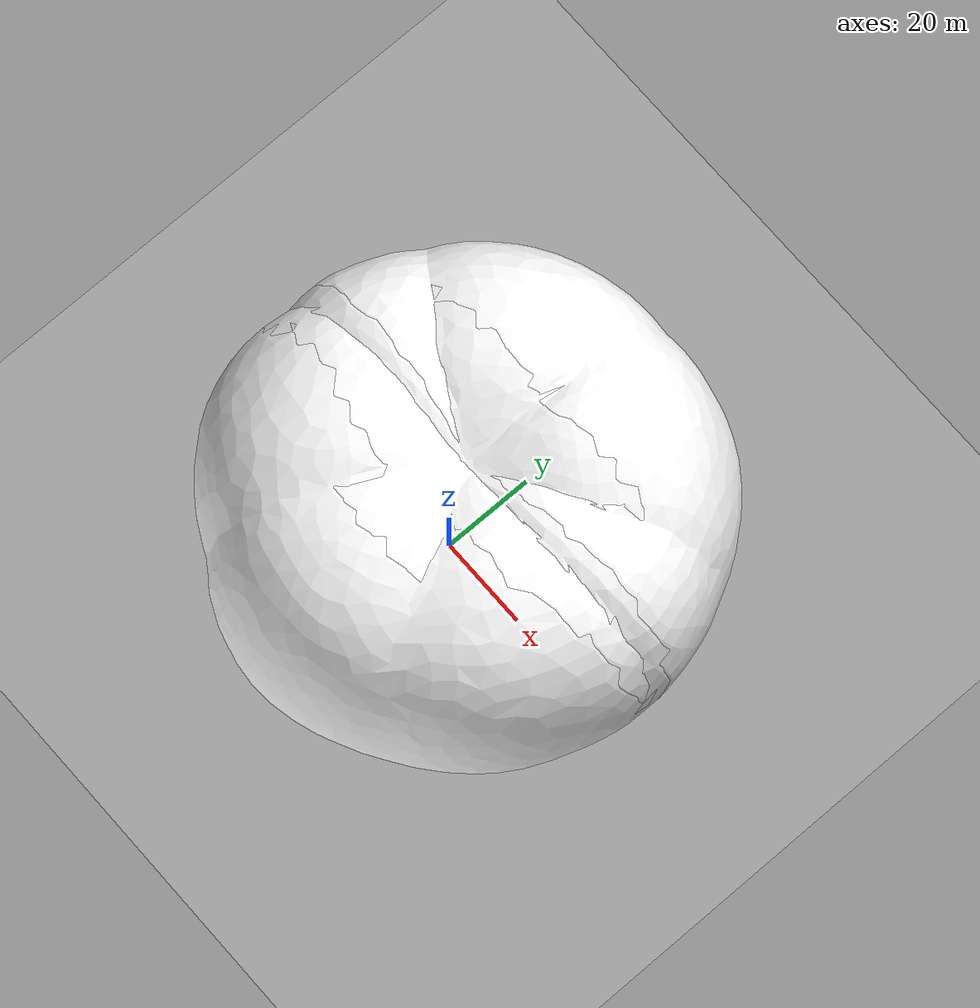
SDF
<?xml version="1.0" ?>
<sdf version="1.5">
  <world name="default">
   <gui>
      <camera name="user_default">
            <pose>16. 2. 13. 0 0.77 3.12</pose>
      </camera>
    </gui>
    <include>
      <uri>model://sun_2</uri>
    </include>
    <scene>
      <ambient>1 1 1 1</ambient>
      <background>0.8 0.8 0.8 1</background>
      <shadows>1</shadows>
    </scene>
    <light name='sun' type='directional'>
       <cast_shadows>1</cast_shadows>
       <pose>0 0 10 0 -0 0</pose>
       <diffuse>0.8 0.8 0.8 1</diffuse>
       <specular>0.8 0.8 0.8 1</specular>
       <attenuation>
          <range>1000</range>
          <constant>0.9</constant>
          <linear>0.01</linear>
          <quadratic>0.001</quadratic>
       </attenuation>
       <direction>-0.5 0.1 -0.9</direction>
       <spot>
          <inner_angle>0</inner_angle>
          <outer_angle>0</outer_angle>
          <falloff>0</falloff>
       </spot>
    </light>
    <include>
      <uri>model://ground_plane</uri>
    </include>
    <include>
      <uri>model://tomato_plant1</uri>
      <name>tomato_plant1</name>
      <pose>0.0 0.0 0 0 0 0</pose>
    </include>
    <include>
      <uri>model://tomato_plant2</uri>
      <name>tomato_plant2</name>
      <pose>0.0 1.0 0 0 0 0</pose>
    </include>
  </world>
</sdf>

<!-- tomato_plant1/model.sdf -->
<sdf version="1.6">
  <model name="tomato_plant1">
      <pose>0 0 0 0 0 0</pose>
      <static>false</static>
      <link name="tomato_tree_link">
        <kinematic> true </kinematic>
        <collision name="collision">
          <pose>0 0 0.7 0 0 0</pose>
          <geometry>
            <box>
              <size>.1 .1 1.4</size>
            </box>
          </geometry>
        </collision>
        <visual name="branch">
          <geometry>
            <mesh>
              <uri>file://tomato_tree1/meshes/tomato.dae</uri>
              <scale>1.4 1.4 1.4</scale>
              <submesh>
                <name>Branch1</name>
              </submesh>
            </mesh>
          </geometry>
          <material>
            <diffuse>1.0 1.0 1.0</diffuse>
            <script>
              <uri>model://tomato_tree1/materials/scripts/</uri>
              <uri>model://tomato_tree1/materials/textures/</uri>
              <name>BranchTexture</name>
            </script>
          </material>
        </visual>
        <visual name="leaf1">
          <geometry>
            <mesh>
              <uri>file://tomato_tree1/meshes/tomato.dae</uri>
              <scale>1.4 1.4 1.4</scale>
              <submesh>
                <name>Leaf1</name>
              </submesh>
            </mesh>
          </geometry>
          <material>
            <diffuse>1.0 1.0 1.0</diffuse>
            <script>
              <uri>model://tomato_tree1/materials/scripts/</uri>
              <uri>model://tomato_tree1/materials/textures/</uri>
              <name>Leaf1Texture</name>
            </script>
          </material>
        </visual>
        <visual name="leaf2">
          <geometry>
            <mesh>
              <uri>file://tomato_tree1/meshes/tomato.dae</uri>
              <scale>1.4 1.4 1.4</scale>
              <submesh>
                <name>Leaf2</name>
              </submesh>
            </mesh>
          </geometry>
          <material>
            <diffuse>1.0 1.0 1.0</diffuse>
            <script>
              <uri>model://tomato_tree1/materials/scripts/</uri>
              <uri>model://tomato_tree1/materials/textures/</uri>
              <name>Leaf2Texture</name>
            </script>
          </material>
        </visual>
        <visual name="blossom1">
          <geometry>
            <mesh>
              <uri>file://tomato_tree1/meshes/tomato.dae</uri>
              <scale>1.4 1.4 1.4</scale>
              <submesh>
                <name>Blossom1</name>
              </submesh>
            </mesh>
          </geometry>
          <material>
            <diffuse>1.0 1.0 1.0</diffuse>
            <script>
              <uri>model://tomato_tree1/materials/scripts/</uri>
              <uri>model://tomato_tree1/materials/textures/</uri>
              <name>Blossom1Texture</name>
            </script>
          </material>
        </visual>
        <visual name="blossom2">
          <geometry>
            <mesh>
              <uri>file://tomato_tree1/meshes/tomato.dae</uri>
              <scale>1.4 1.4 1.4</scale>
              <submesh>
                <name>Blossom2</name>
              </submesh>
            </mesh>
          </geometry>
          <material>
            <diffuse>1.0 1.0 1.0</diffuse>
            <script>
              <uri>model://tomato_tree1/materials/scripts/</uri>
              <uri>model://tomato_tree1/materials/textures/</uri>
              <name>Blossom2Texture</name>
            </script>
          </material>
        </visual>
        <visual name="blossom3">
          <geometry>
            <mesh>
              <uri>file://tomato_tree1/meshes/tomato.dae</uri>
              <scale>1.4 1.4 1.4</scale>
              <submesh>
                <name>Blossom3</name>
              </submesh>
            </mesh>
          </geometry>
          <material>
            <diffuse>1.0 1.0 1.0</diffuse>
            <script>
              <uri>model://tomato_tree1/materials/scripts/</uri>
              <uri>model://tomato_tree1/materials/textures/</uri>
              <name>Blossom3Texture</name>
            </script>
          </material>
        </visual>
       </link>
       <link name="tomato1_link">
        <pose>-0.05394015312194824 -0.16384320259094237 0.7056782789230346 0.05 0.05 0.25</pose>
        <inertial>
          <mass>0.1</mass>
          <inertia>
            <ixx>0.00009</ixx>
            <ixy>0</ixy>
            <ixz>0</ixz>
            <iyy>0.00009</iyy>
            <iyz>0</iyz>
            <izz>0.00009</izz>
          </inertia>
        </inertial>
        <collision name="collision">
          <geometry>
            <mesh>
              <scale>0.001 0.001 0.001</scale>
              <uri>file://tomato_fruit1/meshes/tomato.stl</uri>
            </mesh>
          </geometry>
        </collision>
        <visual name="fruit">
          <geometry>
            <mesh>
              <scale>0.001 0.001 0.001</scale>
              <uri>file://tomato_fruit1/meshes/tomato.stl</uri>
            </mesh>
          </geometry>
          <material>
            <diffuse>1.0 1.0 1.0</diffuse>
            <script>
              <uri>model://tomato_fruit1/materials/scripts/</uri>
              <uri>model://tomato_fruit1/materials/textures/</uri>
              <name>Fruit1Texture</name>
            </script>
          </material>
        </visual>
      </link>
      <joint name="joint_tomato1" type="fixed">
        <parent>tomato_tree_link</parent>
        <child>tomato1_link</child>
      </joint>
      <plugin name="detachable_joint_plugin1" filename="libDetachableJointPlugin.so">
        <joint_name>joint_tomato1</joint_name>
        <force_threshold>30.0</force_threshold>
        <link_name>tomato1_link</link_name>
      </plugin>
      <link name="tomato2_link">
        <pose>0.13146963119506835 0.006717109680175781 1.0723974800109863 0.2 0 0</pose>
        <inertial>
          <mass>0.1</mass>
          <inertia>
            <ixx>0.00009</ixx>
            <ixy>0</ixy>
            <ixz>0</ixz>
            <iyy>0.00009</iyy>
            <iyz>0</iyz>
            <izz>0.00009</izz>
          </inertia>
        </inertial>
        <collision name="collision">
          <geometry>
            <mesh>
              <scale>0.001 0.001 0.001</scale>
              <uri>file://tomato_fruit1/meshes/tomato.stl</uri>
            </mesh>
          </geometry>
        </collision>
        <visual name="fruit">
          <geometry>
            <mesh>
              <scale>0.001 0.001 0.001</scale>
              <uri>file://tomato_fruit1/meshes/tomato.stl</uri>
            </mesh>
          </geometry>
          <material>
            <diffuse>1.0 1.0 1.0</diffuse>
            <script>
              <uri>model://tomato_fruit1/materials/scripts/</uri>
              <uri>model://tomato_fruit1/materials/textures/</uri>
              <name>Fruit1Texture</name>
            </script>
          </material>
        </visual>
      </link>
      <joint name="joint_tomato2" type="fixed">
        <parent>tomato_tree_link</parent>
        <child>tomato2_link</child>
      </joint>
      <plugin name="detachable_joint_plugin2" filename="libDetachableJointPlugin.so">
        <joint_name>joint_tomato2</joint_name>
        <force_threshold>30.0</force_threshold>
        <link_name>tomato2_link</link_name>
      </plugin>
      <link name="tomato3_link">
        <pose>0.18367309570312498 0.04967236518859863 1.0241944408416748 0 0 0</pose>
        <inertial>
          <mass>0.1</mass>
          <inertia>
            <ixx>0.00009</ixx>
            <ixy>0</ixy>
            <ixz>0</ixz>
            <iyy>0.00009</iyy>
            <iyz>0</iyz>
            <izz>0.00009</izz>
          </inertia>
        </inertial>
        <collision name="collision">
          <geometry>
            <mesh>
              <scale>0.001 0.001 0.001</scale>
              <uri>file://tomato_fruit2/meshes/tomato.stl</uri>
            </mesh>
          </geometry>
        </collision>
        <visual name="fruit">
          <geometry>
            <mesh>
              <scale>0.001 0.001 0.001</scale>
              <uri>file://tomato_fruit2/meshes/tomato.stl</uri>
            </mesh>
          </geometry>
          <material>
            <diffuse>1.0 1.0 1.0</diffuse>
            <script>
              <uri>model://tomato_fruit2/materials/scripts/</uri>
              <uri>model://tomato_fruit2/materials/textures/</uri>
              <name>Fruit2Texture</name>
            </script>
          </material>
        </visual>
      </link>
      <joint name="joint_tomato3" type="fixed">
        <parent>tomato_tree_link</parent>
        <child>tomato3_link</child>
      </joint>
      <plugin name="detachable_joint_plugin3" filename="libDetachableJointPlugin.so">
        <joint_name>joint_tomato3</joint_name>
        <force_threshold>30.0</force_threshold>
        <link_name>tomato3_link</link_name>
      </plugin>
      <link name="tomato4_link">
        <pose>0.20033752918243408 0.02009624099731445 0.8659565258026122 0 -0.19999 0</pose>
        <inertial>
          <mass>0.1</mass>
          <inertia>
            <ixx>0.00009</ixx>
            <ixy>0</ixy>
            <ixz>0</ixz>
            <iyy>0.00009</iyy>
            <iyz>0</iyz>
            <izz>0.00009</izz>
          </inertia>
        </inertial>
        <collision name="collision">
          <geometry>
            <mesh>
              <scale>0.001 0.001 0.001</scale>
              <uri>file://tomato_fruit2/meshes/tomato.stl</uri>
            </mesh>
          </geometry>
        </collision>
        <visual name="fruit">
          <geometry>
            <mesh>
              <scale>0.001 0.001 0.001</scale>
              <uri>file://tomato_fruit2/meshes/tomato.stl</uri>
            </mesh>
          </geometry>
          <material>
            <diffuse>1.0 1.0 1.0</diffuse>
            <script>
              <uri>model://tomato_fruit2/materials/scripts/</uri>
              <uri>model://tomato_fruit2/materials/textures/</uri>
              <name>Fruit2Texture</name>
            </script>
          </material>
        </visual>
      </link>
      <joint name="joint_tomato4" type="fixed">
        <parent>tomato_tree_link</parent>
        <child>tomato4_link</child>
      </joint>
      <plugin name="detachable_joint_plugin4" filename="libDetachableJointPlugin.so">
        <joint_name>joint_tomato4</joint_name>
        <force_threshold>30.0</force_threshold>
        <link_name>tomato4_link</link_name>
      </plugin>
      <link name="tomato5_link">
        <pose>0.14674280166625977 0.035393218994140624 0.9081102076530456 0.35 0 0</pose>
        <inertial>
          <mass>0.1</mass>
          <inertia>
            <ixx>0.00009</ixx>
            <ixy>0</ixy>
            <ixz>0</ixz>
            <iyy>0.00009</iyy>
            <iyz>0</iyz>
            <izz>0.00009</izz>
          </inertia>
        </inertial>
        <collision name="collision">
          <geometry>
            <mesh>
              <scale>0.001 0.001 0.001</scale>
              <uri>file://tomato_fruit3/meshes/tomato.stl</uri>
            </mesh>
          </geometry>
        </collision>
        <visual name="fruit">
          <geometry>
            <mesh>
              <scale>0.001 0.001 0.001</scale>
              <uri>file://tomato_fruit3/meshes/tomato.stl</uri>
            </mesh>
          </geometry>
          <material>
            <diffuse>1.0 1.0 1.0</diffuse>
            <script>
              <uri>model://tomato_fruit3/materials/scripts/</uri>
              <uri>model://tomato_fruit3/materials/textures/</uri>
              <name>Fruit3Texture</name>
            </script>
          </material>
        </visual>
      </link>
      <joint name="joint_tomato5" type="fixed">
        <parent>tomato_tree_link</parent>
        <child>tomato5_link</child>
      </joint>
      <plugin name="detachable_joint_plugin5" filename="libDetachableJointPlugin.so">
        <joint_name>joint_tomato5</joint_name>
        <force_threshold>30.0</force_threshold>
        <link_name>tomato5_link</link_name>
      </plugin>
      <link name="tomato6_link">
        <pose>0.19409005641937255 -0.0120302951431274413 0.9682132468223571 -0.15 0 0</pose>
        <inertial>
          <mass>0.1</mass>
          <inertia>
            <ixx>0.00009</ixx>
            <ixy>0</ixy>
            <ixz>0</ixz>
            <iyy>0.00009</iyy>
            <iyz>0</iyz>
            <izz>0.00009</izz>
          </inertia>
        </inertial>
        <collision name="collision">
          <geometry>
            <mesh>
              <scale>0.001 0.001 0.001</scale>
              <uri>file://tomato_fruit1/meshes/tomato.stl</uri>
            </mesh>
          </geometry>
        </collision>
        <visual name="fruit">
          <geometry>
            <mesh>
              <scale>0.001 0.001 0.001</scale>
              <uri>file://tomato_fruit1/meshes/tomato.stl</uri>
            </mesh>
          </geometry>
          <material>
            <diffuse>1.0 1.0 1.0</diffuse>
            <script>
              <uri>model://tomato_fruit1/materials/scripts/</uri>
              <uri>model://tomato_fruit1/materials/textures/</uri>
              <name>Fruit1Texture</name>
            </script>
          </material>
        </visual>
      </link>
      <joint name="joint_tomato6" type="fixed">
        <parent>tomato_tree_link</parent>
        <child>tomato6_link</child>
      </joint>
      <plugin name="detachable_joint_plugin6" filename="libDetachableJointPlugin.so">
        <joint_name>joint_tomato6</joint_name>
        <force_threshold>30.0</force_threshold>
        <link_name>tomato6_link</link_name>
      </plugin>
      <link name="tomato7_link">
        <pose>-0.07996895313262939 -0.10919609069824218 0.9861317372322081 0 0.3 0</pose>
        <inertial>
          <mass>0.1</mass>
          <inertia>
            <ixx>0.00009</ixx>
            <ixy>0</ixy>
            <ixz>0</ixz>
            <iyy>0.00009</iyy>
            <iyz>0</iyz>
            <izz>0.00009</izz>
          </inertia>
        </inertial>
        <collision name="collision">
          <geometry>
            <mesh>
              <scale>0.001 0.001 0.001</scale>
              <uri>file://tomato_fruit1/meshes/tomato.stl</uri>
            </mesh>
          </geometry>
        </collision>
        <visual name="fruit">
          <geometry>
            <mesh>
              <scale>0.001 0.001 0.001</scale>
              <uri>file://tomato_fruit1/meshes/tomato.stl</uri>
            </mesh>
          </geometry>
          <material>
            <diffuse>1.0 1.0 1.0</diffuse>
            <script>
              <uri>model://tomato_fruit1/materials/scripts/</uri>
              <uri>model://tomato_fruit1/materials/textures/</uri>
              <name>Fruit1Texture</name>
            </script>
          </material>
        </visual>
      </link>
      <joint name="joint_tomato7" type="fixed">
        <parent>tomato_tree_link</parent>
        <child>tomato7_link</child>
      </joint>
      <plugin name="detachable_joint_plugin7" filename="libDetachableJointPlugin.so">
        <joint_name>joint_tomato7</joint_name>
        <force_threshold>30.0</force_threshold>
        <link_name>tomato7_link</link_name>
      </plugin>
      <link name="tomato8_link">
        <pose>-0.04341688156127929 -0.11783113479614257 0.8839171767234801 0 0 0</pose>
        <inertial>
          <mass>0.1</mass>
          <inertia>
            <ixx>0.00009</ixx>
            <ixy>0</ixy>
            <ixz>0</ixz>
            <iyy>0.00009</iyy>
            <iyz>0</iyz>
            <izz>0.00009</izz>
          </inertia>
        </inertial>
        <collision name="collision">
          <geometry>
            <mesh>
              <scale>0.001 0.001 0.001</scale>
              <uri>file://tomato_fruit3/meshes/tomato.stl</uri>
            </mesh>
          </geometry>
        </collision>
        <visual name="fruit">
          <geometry>
            <mesh>
              <scale>0.001 0.001 0.001</scale>
              <uri>file://tomato_fruit3/meshes/tomato.stl</uri>
            </mesh>
          </geometry>
          <material>
            <diffuse>1.0 1.0 1.0</diffuse>
            <script>
              <uri>model://tomato_fruit3/materials/scripts/</uri>
              <uri>model://tomato_fruit3/materials/textures/</uri>
              <name>Fruit3Texture</name>
            </script>
          </material>
        </visual>
      </link>
      <joint name="joint_tomato8" type="fixed">
        <parent>tomato_tree_link</parent>
        <child>tomato8_link</child>
      </joint>
      <plugin name="detachable_joint_plugin8" filename="libDetachableJointPlugin.so">
        <joint_name>joint_tomato8</joint_name>
        <force_threshold>30.0</force_threshold>
        <link_name>tomato8_link</link_name>
      </plugin>
      <link name="tomato9_link">
        <pose>-0.04795904159545898 -0.17980518341064453 0.8225939273834229 -0.1 0 0</pose>
        <inertial>
          <mass>0.1</mass>
          <inertia>
            <ixx>0.00009</ixx>
            <ixy>0</ixy>
            <ixz>0</ixz>
            <iyy>0.00009</iyy>
            <iyz>0</iyz>
            <izz>0.00009</izz>
          </inertia>
        </inertial>
        <collision name="collision">
          <geometry>
            <mesh>
              <scale>0.001 0.001 0.001</scale>
              <uri>file://tomato_fruit2/meshes/tomato.stl</uri>
            </mesh>
          </geometry>
        </collision>
        <visual name="fruit">
          <geometry>
            <mesh>
              <scale>0.001 0.001 0.001</scale>
              <uri>file://tomato_fruit2/meshes/tomato.stl</uri>
            </mesh>
          </geometry>
          <material>
            <diffuse>1.0 1.0 1.0</diffuse>
            <script>
              <uri>model://tomato_fruit2/materials/scripts/</uri>
              <uri>model://tomato_fruit2/materials/textures/</uri>
              <name>Fruit2Texture</name>
            </script>
          </material>
        </visual>
      </link>
      <joint name="joint_tomato9" type="fixed">
        <parent>tomato_tree_link</parent>
        <child>tomato9_link</child>
      </joint>
      <plugin name="detachable_joint_plugin9" filename="libDetachableJointPlugin.so">
        <joint_name>joint_tomato9</joint_name>
        <force_threshold>30.0</force_threshold>
        <link_name>tomato9_link</link_name>
      </plugin>
      <link name="tomato10_link">
        <pose>-0.0930229902267456 -0.1536400318145752 0.7575117468833923 0 0 0</pose>
        <inertial>
          <mass>0.1</mass>
          <inertia>
            <ixx>0.00009</ixx>
            <ixy>0</ixy>
            <ixz>0</ixz>
            <iyy>0.00009</iyy>
            <iyz>0</iyz>
            <izz>0.00009</izz>
          </inertia>
        </inertial>
        <collision name="collision">
          <geometry>
            <mesh>
              <scale>0.001 0.001 0.001</scale>
              <uri>file://tomato_fruit2/meshes/tomato.stl</uri>
            </mesh>
          </geometry>
        </collision>
        <visual name="fruit">
          <geometry>
            <mesh>
              <scale>0.001 0.001 0.001</scale>
              <uri>file://tomato_fruit2/meshes/tomato.stl</uri>
            </mesh>
          </geometry>
          <material>
            <diffuse>1.0 1.0 1.0</diffuse>
            <script>
              <uri>model://tomato_fruit2/materials/scripts/</uri>
              <uri>model://tomato_fruit2/materials/textures/</uri>
              <name>Fruit2Texture</name>
            </script>
          </material>
        </visual>
      </link>
      <joint name="joint_tomato10" type="fixed">
        <parent>tomato_tree_link</parent>
        <child>tomato10_link</child>
      </joint>
      <plugin name="detachable_joint_plugin10" filename="libDetachableJointPlugin.so">
        <joint_name>joint_tomato10</joint_name>
        <force_threshold>30.0</force_threshold>
        <link_name>tomato10_link</link_name>
      </plugin>
      <link name="tomato11_link">
        <pose>0.05919956684112549 -0.14371824264526367 1.4059474744796752 0.05 -0.2 0</pose>
        <inertial>
          <mass>0.1</mass>
          <inertia>
            <ixx>0.00009</ixx>
            <ixy>0</ixy>
            <ixz>0</ixz>
            <iyy>0.00009</iyy>
            <iyz>0</iyz>
            <izz>0.00009</izz>
          </inertia>
        </inertial>
        <collision name="collision">
          <geometry>
            <mesh>
              <scale>0.001 0.001 0.001</scale>
              <uri>file://tomato_fruit3/meshes/tomato.stl</uri>
            </mesh>
          </geometry>
        </collision>
        <visual name="fruit">
          <geometry>
            <mesh>
              <scale>0.001 0.001 0.001</scale>
              <uri>file://tomato_fruit3/meshes/tomato.stl</uri>
            </mesh>
          </geometry>
          <material>
            <diffuse>1.0 1.0 1.0</diffuse>
            <script>
              <uri>model://tomato_fruit3/materials/scripts/</uri>
              <uri>model://tomato_fruit3/materials/textures/</uri>
              <name>Fruit3Texture</name>
            </script>
          </material>
        </visual>
      </link>
      <joint name="joint_tomato11" type="fixed">
        <parent>tomato_tree_link</parent>
        <child>tomato11_link</child>
      </joint>
      <plugin name="detachable_joint_plugin11" filename="libDetachableJointPlugin.so">
        <joint_name>joint_tomato11</joint_name>
        <force_threshold>30.0</force_threshold>
        <link_name>tomato11_link</link_name>
      </plugin>
      <link name="tomato12_link">
        <pose>-0.03117918014526367 -0.09120068550109862 1.4716318130493162 -0.149 0.199 0</pose>
        <inertial>
          <mass>0.1</mass>
          <inertia>
            <ixx>0.00009</ixx>
            <ixy>0</ixy>
            <ixz>0</ixz>
            <iyy>0.00009</iyy>
            <iyz>0</iyz>
            <izz>0.00009</izz>
          </inertia>
        </inertial>
        <collision name="collision">
          <geometry>
            <mesh>
              <scale>0.001 0.001 0.001</scale>
              <uri>file://tomato_fruit1/meshes/tomato.stl</uri>
            </mesh>
          </geometry>
        </collision>
        <visual name="fruit">
          <geometry>
            <mesh>
              <scale>0.001 0.001 0.001</scale>
              <uri>file://tomato_fruit1/meshes/tomato.stl</uri>
            </mesh>
          </geometry>
          <material>
            <diffuse>1.0 1.0 1.0</diffuse>
            <script>
              <uri>model://tomato_fruit1/materials/scripts/</uri>
              <uri>model://tomato_fruit1/materials/textures/</uri>
              <name>Fruit1Texture</name>
            </script>
          </material>
        </visual>
      </link>
      <joint name="joint_tomato12" type="fixed">
        <parent>tomato_tree_link</parent>
        <child>tomato12_link</child>
      </joint>
      <plugin name="detachable_joint_plugin12" filename="libDetachableJointPlugin.so">
        <joint_name>joint_tomato12</joint_name>
        <force_threshold>30.0</force_threshold>
        <link_name>tomato12_link</link_name>
      </plugin>
      <link name="tomato13_link">
        <pose>-0.018955707550048827 -0.15519046783447266 1.373706111907959 -0.15 0 0</pose>
        <inertial>
          <mass>0.1</mass>
          <inertia>
            <ixx>0.00009</ixx>
            <ixy>0</ixy>
            <ixz>0</ixz>
            <iyy>0.00009</iyy>
            <iyz>0</iyz>
            <izz>0.00009</izz>
          </inertia>
        </inertial>
        <collision name="collision">
          <geometry>
            <mesh>
              <scale>0.001 0.001 0.001</scale>
              <uri>file://tomato_fruit1/meshes/tomato.stl</uri>
            </mesh>
          </geometry>
        </collision>
        <visual name="fruit">
          <geometry>
            <mesh>
              <scale>0.001 0.001 0.001</scale>
              <uri>file://tomato_fruit1/meshes/tomato.stl</uri>
            </mesh>
          </geometry>
          <material>
            <diffuse>1.0 1.0 1.0</diffuse>
            <script>
              <uri>model://tomato_fruit1/materials/scripts/</uri>
              <uri>model://tomato_fruit1/materials/textures/</uri>
              <name>Fruit1Texture</name>
            </script>
          </material>
        </visual>
      </link>
      <joint name="joint_tomato13" type="fixed">
        <parent>tomato_tree_link</parent>
        <child>tomato13_link</child>
      </joint>
      <plugin name="detachable_joint_plugin13" filename="libDetachableJointPlugin.so">
        <joint_name>joint_tomato13</joint_name>
        <force_threshold>30.0</force_threshold>
        <link_name>tomato13_link</link_name>
      </plugin>
      <link name="tomato14_link">
        <pose>0.03208340644836425 -0.18436113357543945 1.2985199651718138 -0.399 0 0</pose>
        <inertial>
          <mass>0.1</mass>
          <inertia>
            <ixx>0.00009</ixx>
            <ixy>0</ixy>
            <ixz>0</ixz>
            <iyy>0.00009</iyy>
            <iyz>0</iyz>
            <izz>0.00009</izz>
          </inertia>
        </inertial>
        <collision name="collision">
          <geometry>
            <mesh>
              <scale>0.001 0.001 0.001</scale>
              <uri>file://tomato_fruit3/meshes/tomato.stl</uri>
            </mesh>
          </geometry>
        </collision>
        <visual name="fruit">
          <geometry>
            <mesh>
              <scale>0.001 0.001 0.001</scale>
              <uri>file://tomato_fruit3/meshes/tomato.stl</uri>
            </mesh>
          </geometry>
          <material>
            <diffuse>1.0 1.0 1.0</diffuse>
            <script>
              <uri>model://tomato_fruit3/materials/scripts/</uri>
              <uri>model://tomato_fruit3/materials/textures/</uri>
              <name>Fruit3Texture</name>
            </script>
          </material>
        </visual>
      </link>
      <joint name="joint_tomato14" type="fixed">
        <parent>tomato_tree_link</parent>
        <child>tomato14_link</child>
      </joint>
      <plugin name="detachable_joint_plugin14" filename="libDetachableJointPlugin.so">
        <joint_name>joint_tomato14</joint_name>
        <force_threshold>30.0</force_threshold>
        <link_name>tomato14_link</link_name>
      </plugin>
      <link name="tomato15_link">
        <pose>0.02652597427368164 -0.12390971183776854 1.333142068862915 0.05 -0.2 0</pose>
        <inertial>
          <mass>0.1</mass>
          <inertia>
            <ixx>0.00009</ixx>
            <ixy>0</ixy>
            <ixz>0</ixz>
            <iyy>0.00009</iyy>
            <iyz>0</iyz>
            <izz>0.00009</izz>
          </inertia>
        </inertial>
        <collision name="collision">
          <geometry>
            <mesh>
              <scale>0.001 0.001 0.001</scale>
              <uri>file://tomato_fruit3/meshes/tomato.stl</uri>
            </mesh>
          </geometry>
        </collision>
        <visual name="fruit">
          <geometry>
            <mesh>
              <scale>0.001 0.001 0.001</scale>
              <uri>file://tomato_fruit3/meshes/tomato.stl</uri>
            </mesh>
          </geometry>
          <material>
            <diffuse>1.0 1.0 1.0</diffuse>
            <script>
              <uri>model://tomato_fruit3/materials/scripts/</uri>
              <uri>model://tomato_fruit3/materials/textures/</uri>
              <name>Fruit3Texture</name>
            </script>
          </material>
        </visual>
      </link>
      <joint name="joint_tomato15" type="fixed">
        <parent>tomato_tree_link</parent>
        <child>tomato15_link</child>
      </joint>
      <plugin name="detachable_joint_plugin15" filename="libDetachableJointPlugin.so">
        <joint_name>joint_tomato15</joint_name>
        <force_threshold>30.0</force_threshold>
        <link_name>tomato15_link</link_name>
      </plugin>
      <link name="tomato16_link">
        <pose>0.0024403095245361327 -0.09210624694824218 1.4153467512130737 0 0.2 0</pose>
        <inertial>
          <mass>0.1</mass>
          <inertia>
            <ixx>0.00009</ixx>
            <ixy>0</ixy>
            <ixz>0</ixz>
            <iyy>0.00009</iyy>
            <iyz>0</iyz>
            <izz>0.00009</izz>
          </inertia>
        </inertial>
        <collision name="collision">
          <geometry>
            <mesh>
              <scale>0.001 0.001 0.001</scale>
              <uri>file://tomato_fruit1/meshes/tomato.stl</uri>
            </mesh>
          </geometry>
        </collision>
        <visual name="fruit">
          <geometry>
            <mesh>
              <scale>0.001 0.001 0.001</scale>
              <uri>file://tomato_fruit1/meshes/tomato.stl</uri>
            </mesh>
          </geometry>
          <material>
            <diffuse>1.0 1.0 1.0</diffuse>
            <script>
              <uri>model://tomato_fruit1/materials/scripts/</uri>
              <uri>model://tomato_fruit1/materials/textures/</uri>
              <name>Fruit1Texture</name>
            </script>
          </material>
        </visual>
      </link>
      <joint name="joint_tomato16" type="fixed">
        <parent>tomato_tree_link</parent>
        <child>tomato16_link</child>
      </joint>
      <plugin name="detachable_joint_plugin16" filename="libDetachableJointPlugin.so">
        <joint_name>joint_tomato16</joint_name>
        <force_threshold>30.0</force_threshold>
        <link_name>tomato16_link</link_name>
      </plugin>

      <link name="tomato17_link">
        <pose>0.02202320098876953 -0.1615869140625 1.2361759042739866 0 0 0</pose>
        <inertial>
          <mass>0.1</mass>
          <inertia>
            <ixx>0.00009</ixx>
            <ixy>0</ixy>
            <ixz>0</ixz>
            <iyy>0.00009</iyy>
            <iyz>0</iyz>
            <izz>0.00009</izz>
          </inertia>
        </inertial>
        <collision name="collision">
          <geometry>
            <mesh>
              <scale>0.001 0.001 0.001</scale>
              <uri>file://tomato_fruit2/meshes/tomato.stl</uri>
            </mesh>
          </geometry>
        </collision>
        <visual name="fruit">
          <geometry>
            <mesh>
              <scale>0.001 0.001 0.001</scale>
              <uri>file://tomato_fruit2/meshes/tomato.stl</uri>
            </mesh>
          </geometry>
          <material>
            <diffuse>1.0 1.0 1.0</diffuse>
            <script>
              <uri>model://tomato_fruit2/materials/scripts/</uri>
              <uri>model://tomato_fruit2/materials/textures/</uri>
              <name>Fruit2Texture</name>
            </script>
          </material>
        </visual>
      </link>
      <joint name="joint_tomato17" type="fixed">
        <parent>tomato_tree_link</parent>
        <child>tomato17_link</child>
      </joint>
      <plugin name="detachable_joint_plugin17" filename="libDetachableJointPlugin.so">
        <joint_name>joint_tomato17</joint_name>
        <force_threshold>30.0</force_threshold>
        <link_name>tomato17_link</link_name>
      </plugin>
      <link name="tomato18_link">
        <pose>-0.0681145429611206 0.111094331741333 1.2918913841247557 0.5 0 0</pose>
        <inertial>
          <mass>0.1</mass>
          <inertia>
            <ixx>0.00009</ixx>
            <ixy>0</ixy>
            <ixz>0</ixz>
            <iyy>0.00009</iyy>
            <iyz>0</iyz>
            <izz>0.00009</izz>
          </inertia>
        </inertial>
        <collision name="collision">
          <geometry>
            <mesh>
              <scale>0.001 0.001 0.001</scale>
              <uri>file://tomato_fruit1/meshes/tomato.stl</uri>
            </mesh>
          </geometry>
        </collision>
        <visual name="fruit">
          <geometry>
            <mesh>
              <scale>0.001 0.001 0.001</scale>
              <uri>file://tomato_fruit1/meshes/tomato.stl</uri>
            </mesh>
          </geometry>
          <material>
            <diffuse>1.0 1.0 1.0</diffuse>
            <script>
              <uri>model://tomato_fruit1/materials/scripts/</uri>
              <uri>model://tomato_fruit1/materials/textures/</uri>
              <name>Fruit1Texture</name>
            </script>
          </material>
        </visual>
      </link>
      <joint name="joint_tomato18" type="fixed">
        <parent>tomato_tree_link</parent>
        <child>tomato18_link</child>
      </joint>
      <plugin name="detachable_joint_plugin18" filename="libDetachableJointPlugin.so">
        <joint_name>joint_tomato18</joint_name>
        <force_threshold>30.0</force_threshold>
        <link_name>tomato18_link</link_name>
      </plugin>
      <link name="tomato19_link">
        <pose>-0.0723905086517334 0.08397588729858398 1.2038684248924254 0 0 0</pose>
        <inertial>
          <mass>0.1</mass>
          <inertia>
            <ixx>0.00009</ixx>
            <ixy>0</ixy>
            <ixz>0</ixz>
            <iyy>0.00009</iyy>
            <iyz>0</iyz>
            <izz>0.00009</izz>
          </inertia>
        </inertial>
        <collision name="collision">
          <geometry>
            <mesh>
              <scale>0.001 0.001 0.001</scale>
              <uri>file://tomato_fruit3/meshes/tomato.stl</uri>
            </mesh>
          </geometry>
        </collision>
        <visual name="fruit">
          <geometry>
            <mesh>
              <scale>0.001 0.001 0.001</scale>
              <uri>file://tomato_fruit3/meshes/tomato.stl</uri>
            </mesh>
          </geometry>
          <material>
            <diffuse>1.0 1.0 1.0</diffuse>
            <script>
              <uri>model://tomato_fruit3/materials/scripts/</uri>
              <uri>model://tomato_fruit3/materials/textures/</uri>
              <name>Fruit3Texture</name>
            </script>
          </material>
        </visual>
      </link>
      <joint name="joint_tomato19" type="fixed">
        <parent>tomato_tree_link</parent>
        <child>tomato19_link</child>
      </joint>
      <plugin name="detachable_joint_plugin19" filename="libDetachableJointPlugin.so">
        <joint_name>joint_tomato19</joint_name>
        <force_threshold>30.0</force_threshold>
        <link_name>tomato19_link</link_name>
      </plugin>
      <link name="tomato20_link">
        <pose>-0.15197771549224852 0.09356493759155273 1.146774411201477 -0.149 -0.2 0</pose>
        <inertial>
          <mass>0.1</mass>
          <inertia>
            <ixx>0.00009</ixx>
            <ixy>0</ixy>
            <ixz>0</ixz>
            <iyy>0.00009</iyy>
            <iyz>0</iyz>
            <izz>0.00009</izz>
          </inertia>
        </inertial>
        <collision name="collision">
          <geometry>
            <mesh>
              <scale>0.001 0.001 0.001</scale>
              <uri>file://tomato_fruit3/meshes/tomato.stl</uri>
            </mesh>
          </geometry>
        </collision>
        <visual name="fruit">
          <geometry>
            <mesh>
              <scale>0.001 0.001 0.001</scale>
              <uri>file://tomato_fruit3/meshes/tomato.stl</uri>
            </mesh>
          </geometry>
          <material>
            <diffuse>1.0 1.0 1.0</diffuse>
            <script>
              <uri>model://tomato_fruit3/materials/scripts/</uri>
              <uri>model://tomato_fruit3/materials/textures/</uri>
              <name>Fruit3Texture</name>
            </script>
          </material>
        </visual>
      </link>
      <joint name="joint_tomato20" type="fixed">
        <parent>tomato_tree_link</parent>
        <child>tomato20_link</child>
      </joint>
      <plugin name="detachable_joint_plugin20" filename="libDetachableJointPlugin.so">
        <joint_name>joint_tomato20</joint_name>
        <force_threshold>30.0</force_threshold>
        <link_name>tomato20_link</link_name>
      </plugin>
      <link name="tomato21_link">
        <pose>-0.11268565654754638 0.14520302772521972 1.0995657796859741 0.5 0 0</pose>
        <inertial>
          <mass>0.1</mass>
          <inertia>
            <ixx>0.00009</ixx>
            <ixy>0</ixy>
            <ixz>0</ixz>
            <iyy>0.00009</iyy>
            <iyz>0</iyz>
            <izz>0.00009</izz>
          </inertia>
        </inertial>
        <collision name="collision">
          <geometry>
            <mesh>
              <scale>0.001 0.001 0.001</scale>
              <uri>file://tomato_fruit2/meshes/tomato.stl</uri>
            </mesh>
          </geometry>
        </collision>
        <visual name="fruit">
          <geometry>
            <mesh>
              <scale>0.001 0.001 0.001</scale>
              <uri>file://tomato_fruit2/meshes/tomato.stl</uri>
            </mesh>
          </geometry>
          <material>
            <diffuse>1.0 1.0 1.0</diffuse>
            <script>
              <uri>model://tomato_fruit2/materials/scripts/</uri>
              <uri>model://tomato_fruit2/materials/textures/</uri>
              <name>Fruit2Texture</name>
            </script>
          </material>
        </visual>
      </link>
      <joint name="joint_tomato21" type="fixed">
        <parent>tomato_tree_link</parent>
        <child>tomato21_link</child>
      </joint>
      <plugin name="detachable_joint_plugin21" filename="libDetachableJointPlugin.so">
        <joint_name>joint_tomato21</joint_name>
        <force_threshold>30.0</force_threshold>
        <link_name>tomato21_link</link_name>
      </plugin>
      <link name="tomato22_link">
        <pose>-0.12110424041748045 0.09839344024658203 1.0475120978355407 -0.25 0 0</pose>
        <inertial>
          <mass>0.1</mass>
          <inertia>
            <ixx>0.00009</ixx>
            <ixy>0</ixy>
            <ixz>0</ixz>
            <iyy>0.00009</iyy>
            <iyz>0</iyz>
            <izz>0.00009</izz>
          </inertia>
        </inertial>
        <collision name="collision">
          <geometry>
            <mesh>
              <scale>0.001 0.001 0.001</scale>
              <uri>file://tomato_fruit2/meshes/tomato.stl</uri>
            </mesh>
          </geometry>
        </collision>
        <visual name="fruit">
          <geometry>
            <mesh>
              <scale>0.001 0.001 0.001</scale>
              <uri>file://tomato_fruit2/meshes/tomato.stl</uri>
            </mesh>
          </geometry>
          <material>
            <diffuse>1.0 1.0 1.0</diffuse>
            <script>
              <uri>model://tomato_fruit2/materials/scripts/</uri>
              <uri>model://tomato_fruit2/materials/textures/</uri>
              <name>Fruit2Texture</name>
            </script>
          </material>
        </visual>
      </link>
      <joint name="joint_tomato22" type="fixed">
        <parent>tomato_tree_link</parent>
        <child>tomato22_link</child>
      </joint>
      <plugin name="detachable_joint_plugin22" filename="libDetachableJointPlugin.so">
        <joint_name>joint_tomato22</joint_name>
        <force_threshold>30.0</force_threshold>
        <link_name>tomato22_link</link_name>
      </plugin>
      <link name="tomato23_link">
        <pose>0.1378769874572754 -0.04001514434814453 1.1527520394325255 0 -0.3 0</pose>
        <inertial>
          <mass>0.1</mass>
          <inertia>
            <ixx>0.00009</ixx>
            <ixy>0</ixy>
            <ixz>0</ixz>
            <iyy>0.00009</iyy>
            <iyz>0</iyz>
            <izz>0.00009</izz>
          </inertia>
        </inertial>
        <collision name="collision">
          <geometry>
            <mesh>
              <scale>0.001 0.001 0.001</scale>
              <uri>file://tomato_fruit1/meshes/tomato.stl</uri>
            </mesh>
          </geometry>
        </collision>
        <visual name="fruit">
          <geometry>
            <mesh>
              <scale>0.001 0.001 0.001</scale>
              <uri>file://tomato_fruit1/meshes/tomato.stl</uri>
            </mesh>
          </geometry>
          <material>
            <diffuse>1.0 1.0 1.0</diffuse>
            <script>
              <uri>model://tomato_fruit1/materials/scripts/</uri>
              <uri>model://tomato_fruit1/materials/textures/</uri>
              <name>Fruit1Texture</name>
            </script>
          </material>
        </visual>
      </link>
      <joint name="joint_tomato23" type="fixed">
        <parent>tomato_tree_link</parent>
        <child>tomato23_link</child>
      </joint>
      <plugin name="detachable_joint_plugin23" filename="libDetachableJointPlugin.so">
        <joint_name>joint_tomato23</joint_name>
        <force_threshold>30.0</force_threshold>
        <link_name>tomato23_link</link_name>
      </plugin>
    </model>
</sdf>

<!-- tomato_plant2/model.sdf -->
<sdf version="1.6">
<model name="tomato_plant2">
      <pose>0 0 0 0 0 0</pose>
      <static>false</static>
      <link name="tomato_tree_link">
        <kinematic> true </kinematic>
        <collision name="collision">
          <pose>0 0 0.7 0 0 0</pose>
          <geometry>
            <box>
              <size>.1 .1 1.4</size>
            </box>
          </geometry>
        </collision>
        <visual name="branch">
          <geometry>
            <mesh>
              <uri>file://tomato_tree2/meshes/tomato.dae</uri>
              <scale>1.4 1.4 1.4</scale>
              <submesh>
                <name>Branch1</name>
              </submesh>
            </mesh>
          </geometry>
          <material>
            <diffuse>1.0 1.0 1.0</diffuse>
            <script>
              <uri>model://tomato_tree2/materials/scripts/</uri>
              <uri>model://tomato_tree2/materials/textures/</uri>
              <name>BranchTexture</name>
            </script>
          </material>
        </visual>
        <visual name="leaf1">
          <geometry>
            <mesh>
              <uri>file://tomato_tree2/meshes/tomato.dae</uri>
              <scale>1.4 1.4 1.4</scale>
              <submesh>
                <name>Leaf1</name>
              </submesh>
            </mesh>
          </geometry>
          <material>
            <diffuse>1.0 1.0 1.0</diffuse>
            <script>
              <uri>model://tomato_tree2/materials/scripts/</uri>
              <uri>model://tomato_tree2/materials/textures/</uri>
              <name>Leaf1Texture</name>
            </script>
          </material>
        </visual>
        <visual name="leaf2">
          <geometry>
            <mesh>
              <uri>file://tomato_tree2/meshes/tomato.dae</uri>
              <scale>1.4 1.4 1.4</scale>
              <submesh>
                <name>Leaf2</name>
              </submesh>
            </mesh>
          </geometry>
          <material>
            <diffuse>1.0 1.0 1.0</diffuse>
            <script>
              <uri>model://tomato_tree2/materials/scripts/</uri>
              <uri>model://tomato_tree2/materials/textures/</uri>
              <name>Leaf2Texture</name>
            </script>
          </material>
        </visual>
        <visual name="blossom1">
          <geometry>
            <mesh>
              <uri>file://tomato_tree2/meshes/tomato.dae</uri>
              <scale>1.4 1.4 1.4</scale>
              <submesh>
                <name>Blossom1</name>
              </submesh>
            </mesh>
          </geometry>
          <material>
            <diffuse>1.0 1.0 1.0</diffuse>
            <script>
              <uri>model://tomato_tree2/materials/scripts/</uri>
              <uri>model://tomato_tree2/materials/textures/</uri>
              <name>Blossom1Texture</name>
            </script>
          </material>
        </visual>
        <visual name="blossom2">
          <geometry>
            <mesh>
              <uri>file://tomato_tree2/meshes/tomato.dae</uri>
              <scale>1.4 1.4 1.4</scale>
              <submesh>
                <name>Blossom2</name>
              </submesh>
            </mesh>
          </geometry>
          <material>
            <diffuse>1.0 1.0 1.0</diffuse>
            <script>
              <uri>model://tomato_tree2/materials/scripts/</uri>
              <uri>model://tomato_tree2/materials/textures/</uri>
              <name>Blossom2Texture</name>
            </script>
          </material>
        </visual>
        <visual name="blossom3">
          <geometry>
            <mesh>
              <uri>file://tomato_tree2/meshes/tomato.dae</uri>
              <scale>1.4 1.4 1.4</scale>
              <submesh>
                <name>Blossom3</name>
              </submesh>
            </mesh>
          </geometry>
          <material>
            <diffuse>1.0 1.0 1.0</diffuse>
            <script>
              <uri>model://tomato_tree2/materials/scripts/</uri>
              <uri>model://tomato_tree2/materials/textures/</uri>
              <name>Blossom3Texture</name>
            </script>
          </material>
        </visual>
      </link>
      <link name="tomato1_link">
        <pose>-0.0066316604614257806 -0.19216344356536863 0.6168960587978363 -0.05 0.1 0</pose>
        <inertial>
          <mass>0.1</mass>
          <inertia>
            <ixx>0.00009</ixx>
            <ixy>0</ixy>
            <ixz>0</ixz>
            <iyy>0.00009</iyy>
            <iyz>0</iyz>
            <izz>0.00009</izz>
          </inertia>
        </inertial>
        <collision name="collision">
          <geometry>
            <mesh>
              <scale>0.001 0.001 0.001</scale>
              <uri>file://tomato_fruit1/meshes/tomato.stl</uri>
            </mesh>
          </geometry>
        </collision>
        <visual name="fruit">
          <geometry>
            <mesh>
              <scale>0.001 0.001 0.001</scale>
              <uri>file://tomato_fruit1/meshes/tomato.stl</uri>
            </mesh>
          </geometry>
          <material>
            <diffuse>1.0 1.0 1.0</diffuse>
            <script>
              <uri>model://tomato_fruit1/materials/scripts/</uri>
              <uri>model://tomato_fruit1/materials/textures/</uri>
              <name>Fruit1Texture</name>
            </script>
          </material>
        </visual>
      </link>
      <joint name="joint_tomato1" type="fixed">
        <parent>tomato_tree_link</parent>
        <child>tomato1_link</child>
      </joint>
      <plugin name="detachable_joint_plugin1" filename="libDetachableJointPlugin.so">
        <joint_name>joint_tomato1</joint_name>
        <force_threshold>30.0</force_threshold>
        <link_name>tomato1_link</link_name>
      </plugin>
      <link name="tomato2_link">
        <pose>0.029487323760986325 -0.21878004074096677 0.694796359539032 -0.25 0.1 0</pose>
        <inertial>
          <mass>0.1</mass>
          <inertia>
            <ixx>0.00009</ixx>
            <ixy>0</ixy>
            <ixz>0</ixz>
            <iyy>0.00009</iyy>
            <iyz>0</iyz>
            <izz>0.00009</izz>
          </inertia>
        </inertial>
        <collision name="collision">
          <geometry>
            <mesh>
              <scale>0.001 0.001 0.001</scale>
              <uri>file://tomato_fruit3/meshes/tomato.stl</uri>
            </mesh>
          </geometry>
        </collision>
        <visual name="fruit">
          <geometry>
            <mesh>
              <scale>0.001 0.001 0.001</scale>
              <uri>file://tomato_fruit3/meshes/tomato.stl</uri>
            </mesh>
          </geometry>
          <material>
            <diffuse>1.0 1.0 1.0</diffuse>
            <script>
              <uri>model://tomato_fruit3/materials/scripts/</uri>
              <uri>model://tomato_fruit3/materials/textures/</uri>
              <name>Fruit3Texture</name>
            </script>
          </material>
        </visual>
      </link>
      <joint name="joint_tomato2" type="fixed">
        <parent>tomato_tree_link</parent>
        <child>tomato2_link</child>
      </joint>
      <plugin name="detachable_joint_plugin2" filename="libDetachableJointPlugin.so">
        <joint_name>joint_tomato2</joint_name>
        <force_threshold>30.0</force_threshold>
        <link_name>tomato2_link</link_name>
      </plugin>
      <link name="tomato3_link">
        <pose>0.019719409942626952 -0.13977839946746826 0.7212287902832031 0 -0.25 0</pose>
        <inertial>
          <mass>0.1</mass>
          <inertia>
            <ixx>0.00009</ixx>
            <ixy>0</ixy>
            <ixz>0</ixz>
            <iyy>0.00009</iyy>
            <iyz>0</iyz>
            <izz>0.00009</izz>
          </inertia>
        </inertial>
        <collision name="collision">
          <geometry>
            <mesh>
              <scale>0.001 0.001 0.001</scale>
              <uri>file://tomato_fruit3/meshes/tomato.stl</uri>
            </mesh>
          </geometry>
        </collision>
        <visual name="fruit">
          <geometry>
            <mesh>
              <scale>0.001 0.001 0.001</scale>
              <uri>file://tomato_fruit3/meshes/tomato.stl</uri>
            </mesh>
          </geometry>
          <material>
            <diffuse>1.0 1.0 1.0</diffuse>
            <script>
              <uri>model://tomato_fruit3/materials/scripts/</uri>
              <uri>model://tomato_fruit3/materials/textures/</uri>
              <name>Fruit3Texture</name>
            </script>
          </material>
        </visual>
      </link>
      <joint name="joint_tomato3" type="fixed">
        <parent>tomato_tree_link</parent>
        <child>tomato3_link</child>
      </joint>
      <plugin name="detachable_joint_plugin3" filename="libDetachableJointPlugin.so">
        <joint_name>joint_tomato3</joint_name>
        <force_threshold>30.0</force_threshold>
        <link_name>tomato3_link</link_name>
      </plugin>
      <link name="tomato4_link">
        <pose>-0.02073845863342285 -0.17099740505218505 0.7717585062980652 -0.2 0.25 0</pose>
        <inertial>
          <mass>0.1</mass>
          <inertia>
            <ixx>0.00009</ixx>
            <ixy>0</ixy>
            <ixz>0</ixz>
            <iyy>0.00009</iyy>
            <iyz>0</iyz>
            <izz>0.00009</izz>
          </inertia>
        </inertial>
        <collision name="collision">
          <geometry>
            <mesh>
              <scale>0.001 0.001 0.001</scale>
              <uri>file://tomato_fruit2/meshes/tomato.stl</uri>
            </mesh>
          </geometry>
        </collision>
        <visual name="fruit">
          <geometry>
            <mesh>
              <scale>0.001 0.001 0.001</scale>
              <uri>file://tomato_fruit2/meshes/tomato.stl</uri>
            </mesh>
          </geometry>
          <material>
            <diffuse>1.0 1.0 1.0</diffuse>
            <script>
              <uri>model://tomato_fruit2/materials/scripts/</uri>
              <uri>model://tomato_fruit2/materials/textures/</uri>
              <name>Fruit2Texture</name>
            </script>
          </material>
        </visual>
      </link>
      <joint name="joint_tomato4" type="fixed">
        <parent>tomato_tree_link</parent>
        <child>tomato4_link</child>
      </joint>
      <plugin name="detachable_joint_plugin4" filename="libDetachableJointPlugin.so">
        <joint_name>joint_tomato4</joint_name>
        <force_threshold>30.0</force_threshold>
        <link_name>tomato4_link</link_name>
      </plugin>
      <link name="tomato5_link">
        <pose>0.06358890533447266 -0.13759399890899658 0.7987638592720031 0 -0.25 0</pose>
        <inertial>
          <mass>0.1</mass>
          <inertia>
            <ixx>0.00009</ixx>
            <ixy>0</ixy>
            <ixz>0</ixz>
            <iyy>0.00009</iyy>
            <iyz>0</iyz>
            <izz>0.00009</izz>
          </inertia>
        </inertial>
        <collision name="collision">
          <geometry>
            <mesh>
              <scale>0.001 0.001 0.001</scale>
              <uri>file://tomato_fruit1/meshes/tomato.stl</uri>
            </mesh>
          </geometry>
        </collision>
        <visual name="fruit">
          <geometry>
            <mesh>
              <scale>0.001 0.001 0.001</scale>
              <uri>file://tomato_fruit1/meshes/tomato.stl</uri>
            </mesh>
          </geometry>
          <material>
            <diffuse>1.0 1.0 1.0</diffuse>
            <script>
              <uri>model://tomato_fruit1/materials/scripts/</uri>
              <uri>model://tomato_fruit1/materials/textures/</uri>
              <name>Fruit1Texture</name>
            </script>
          </material>
        </visual>
      </link>
      <joint name="joint_tomato5" type="fixed">
        <parent>tomato_tree_link</parent>
        <child>tomato5_link</child>
      </joint>
      <plugin name="detachable_joint_plugin5" filename="libDetachableJointPlugin.so">
        <joint_name>joint_tomato5</joint_name>
        <force_threshold>30.0</force_threshold>
        <link_name>tomato5_link</link_name>
      </plugin>
      <link name="tomato6_link">
        <pose>0.013982629776000975 -0.07330748081207275 0.8062263345718383 0 0.15 0</pose>
        <inertial>
          <mass>0.1</mass>
          <inertia>
            <ixx>0.00009</ixx>
            <ixy>0</ixy>
            <ixz>0</ixz>
            <iyy>0.00009</iyy>
            <iyz>0</iyz>
            <izz>0.00009</izz>
          </inertia>
        </inertial>
        <collision name="collision">
          <geometry>
            <mesh>
              <scale>0.001 0.001 0.001</scale>
              <uri>file://tomato_fruit3/meshes/tomato.stl</uri>
            </mesh>
          </geometry>
        </collision>
        <visual name="fruit">
          <geometry>
            <mesh>
              <scale>0.001 0.001 0.001</scale>
              <uri>file://tomato_fruit3/meshes/tomato.stl</uri>
            </mesh>
          </geometry>
          <material>
            <diffuse>1.0 1.0 1.0</diffuse>
            <script>
              <uri>model://tomato_fruit3/materials/scripts/</uri>
              <uri>model://tomato_fruit3/materials/textures/</uri>
              <name>Fruit3Texture</name>
            </script>
          </material>
        </visual>
      </link>
      <joint name="joint_tomato6" type="fixed">
        <parent>tomato_tree_link</parent>
        <child>tomato6_link</child>
      </joint>
      <plugin name="detachable_joint_plugin6" filename="libDetachableJointPlugin.so">
        <joint_name>joint_tomato6</joint_name>
        <force_threshold>30.0</force_threshold>
        <link_name>tomato6_link</link_name>
      </plugin>
      <link name="tomato7_link">
        <pose>-0.040427827835083 -0.06760017871856688 0.8667127609252929 0 0.35 0</pose>
        <inertial>
          <mass>0.1</mass>
          <inertia>
            <ixx>0.00009</ixx>
            <ixy>0</ixy>
            <ixz>0</ixz>
            <iyy>0.00009</iyy>
            <iyz>0</iyz>
            <izz>0.00009</izz>
          </inertia>
        </inertial>
        <collision name="collision">
          <geometry>
            <mesh>
              <scale>0.001 0.001 0.001</scale>
              <uri>file://tomato_fruit2/meshes/tomato.stl</uri>
            </mesh>
          </geometry>
        </collision>
        <visual name="fruit">
          <geometry>
            <mesh>
              <scale>0.001 0.001 0.001</scale>
              <uri>file://tomato_fruit2/meshes/tomato.stl</uri>
            </mesh>
          </geometry>
          <material>
            <diffuse>1.0 1.0 1.0</diffuse>
            <script>
              <uri>model://tomato_fruit2/materials/scripts/</uri>
              <uri>model://tomato_fruit2/materials/textures/</uri>
              <name>Fruit2Texture</name>
            </script>
          </material>
        </visual>
      </link>
      <joint name="joint_tomato7" type="fixed">
        <parent>tomato_tree_link</parent>
        <child>tomato7_link</child>
      </joint>
      <plugin name="detachable_joint_plugin7" filename="libDetachableJointPlugin.so">
        <joint_name>joint_tomato7</joint_name>
        <force_threshold>30.0</force_threshold>
        <link_name>tomato7_link</link_name>
      </plugin>
      <link name="tomato8_link">
        <pose>0.15754432678222655 0.14312694072723386 0.7795005249977112 0 -0.25 0</pose>
        <inertial>
          <mass>0.1</mass>
          <inertia>
            <ixx>0.00009</ixx>
            <ixy>0</ixy>
            <ixz>0</ixz>
            <iyy>0.00009</iyy>
            <iyz>0</iyz>
            <izz>0.00009</izz>
          </inertia>
        </inertial>
        <collision name="collision">
          <geometry>
            <mesh>
              <scale>0.001 0.001 0.001</scale>
              <uri>file://tomato_fruit2/meshes/tomato.stl</uri>
            </mesh>
          </geometry>
        </collision>
        <visual name="fruit">
          <geometry>
            <mesh>
              <scale>0.001 0.001 0.001</scale>
              <uri>file://tomato_fruit2/meshes/tomato.stl</uri>
            </mesh>
          </geometry>
          <material>
            <diffuse>1.0 1.0 1.0</diffuse>
            <script>
              <uri>model://tomato_fruit2/materials/scripts/</uri>
              <uri>model://tomato_fruit2/materials/textures/</uri>
              <name>Fruit2Texture</name>
            </script>
          </material>
        </visual>
      </link>
      <joint name="joint_tomato8" type="fixed">
        <parent>tomato_tree_link</parent>
        <child>tomato8_link</child>
      </joint>
      <plugin name="detachable_joint_plugin8" filename="libDetachableJointPlugin.so">
        <joint_name>joint_tomato8</joint_name>
        <force_threshold>30.0</force_threshold>
        <link_name>tomato8_link</link_name>
      </plugin>
      <link name="tomato9_link">
        <pose>0.17055764198303222 0.08876463174819946 0.8600858650207519 0 -0.15 0</pose>
        <inertial>
          <mass>0.1</mass>
          <inertia>
            <ixx>0.00009</ixx>
            <ixy>0</ixy>
            <ixz>0</ixz>
            <iyy>0.00009</iyy>
            <iyz>0</iyz>
            <izz>0.00009</izz>
          </inertia>
        </inertial>
        <collision name="collision">
          <geometry>
            <mesh>
              <scale>0.001 0.001 0.001</scale>
              <uri>file://tomato_fruit2/meshes/tomato.stl</uri>
            </mesh>
          </geometry>
        </collision>
        <visual name="fruit">
          <geometry>
            <mesh>
              <scale>0.001 0.001 0.001</scale>
              <uri>file://tomato_fruit2/meshes/tomato.stl</uri>
            </mesh>
          </geometry>
          <material>
            <diffuse>1.0 1.0 1.0</diffuse>
            <script>
              <uri>model://tomato_fruit2/materials/scripts/</uri>
              <uri>model://tomato_fruit2/materials/textures/</uri>
              <name>Fruit2Texture</name>
            </script>
          </material>
        </visual>
      </link>
      <joint name="joint_tomato9" type="fixed">
        <parent>tomato_tree_link</parent>
        <child>tomato9_link</child>
      </joint>
      <plugin name="detachable_joint_plugin9" filename="libDetachableJointPlugin.so">
        <joint_name>joint_tomato9</joint_name>
        <force_threshold>30.0</force_threshold>
        <link_name>tomato9_link</link_name>
      </plugin>
      <link name="tomato10_link">
        <pose>0.15251517295837402 0.15675978422164915 0.8993290781974792 0.25 0 0</pose>
        <inertial>
          <mass>0.1</mass>
          <inertia>
            <ixx>0.00009</ixx>
            <ixy>0</ixy>
            <ixz>0</ixz>
            <iyy>0.00009</iyy>
            <iyz>0</iyz>
            <izz>0.00009</izz>
          </inertia>
        </inertial>
        <collision name="collision">
          <geometry>
            <mesh>
              <scale>0.001 0.001 0.001</scale>
              <uri>file://tomato_fruit1/meshes/tomato.stl</uri>
            </mesh>
          </geometry>
        </collision>
        <visual name="fruit">
          <geometry>
            <mesh>
              <scale>0.001 0.001 0.001</scale>
              <uri>file://tomato_fruit1/meshes/tomato.stl</uri>
            </mesh>
          </geometry>
          <material>
            <diffuse>1.0 1.0 1.0</diffuse>
            <script>
              <uri>model://tomato_fruit1/materials/scripts/</uri>
              <uri>model://tomato_fruit1/materials/textures/</uri>
              <name>Fruit1Texture</name>
            </script>
          </material>
        </visual>
      </link>
      <joint name="joint_tomato10" type="fixed">
        <parent>tomato_tree_link</parent>
        <child>tomato10_link</child>
      </joint>
      <plugin name="detachable_joint_plugin10" filename="libDetachableJointPlugin.so">
        <joint_name>joint_tomato10</joint_name>
        <force_threshold>30.0</force_threshold>
        <link_name>tomato10_link</link_name>
      </plugin>
      <link name="tomato11_link">
        <pose>0.10660724639892577 0.08952797889709472 0.9110912179946898 0 0.15 0</pose>
        <inertial>
          <mass>0.1</mass>
          <inertia>
            <ixx>0.00009</ixx>
            <ixy>0</ixy>
            <ixz>0</ixz>
            <iyy>0.00009</iyy>
            <iyz>0</iyz>
            <izz>0.00009</izz>
          </inertia>
        </inertial>
        <collision name="collision">
          <geometry>
            <mesh>
              <scale>0.001 0.001 0.001</scale>
              <uri>file://tomato_fruit2/meshes/tomato.stl</uri>
            </mesh>
          </geometry>
        </collision>
        <visual name="fruit">
          <geometry>
            <mesh>
              <scale>0.001 0.001 0.001</scale>
              <uri>file://tomato_fruit2/meshes/tomato.stl</uri>
            </mesh>
          </geometry>
          <material>
            <diffuse>1.0 1.0 1.0</diffuse>
            <script>
              <uri>model://tomato_fruit2/materials/scripts/</uri>
              <uri>model://tomato_fruit2/materials/textures/</uri>
              <name>Fruit2Texture</name>
            </script>
          </material>
        </visual>
      </link>
      <joint name="joint_tomato11" type="fixed">
        <parent>tomato_tree_link</parent>
        <child>tomato11_link</child>
      </joint>
      <plugin name="detachable_joint_plugin11" filename="libDetachableJointPlugin.so">
        <joint_name>joint_tomato11</joint_name>
        <force_threshold>30.0</force_threshold>
        <link_name>tomato11_link</link_name>
      </plugin>
      <link name="tomato12_link">
        <pose>0.07804517745971679 0.03802999258041381 0.9582298822402954 0 -0.15 0</pose>
        <inertial>
          <mass>0.1</mass>
          <inertia>
            <ixx>0.00009</ixx>
            <ixy>0</ixy>
            <ixz>0</ixz>
            <iyy>0.00009</iyy>
            <iyz>0</iyz>
            <izz>0.00009</izz>
          </inertia>
        </inertial>
        <collision name="collision">
          <geometry>
            <mesh>
              <scale>0.001 0.001 0.001</scale>
              <uri>file://tomato_fruit1/meshes/tomato.stl</uri>
            </mesh>
          </geometry>
        </collision>
        <visual name="fruit">
          <geometry>
            <mesh>
              <scale>0.001 0.001 0.001</scale>
              <uri>file://tomato_fruit1/meshes/tomato.stl</uri>
            </mesh>
          </geometry>
          <material>
            <diffuse>1.0 1.0 1.0</diffuse>
            <script>
              <uri>model://tomato_fruit1/materials/scripts/</uri>
              <uri>model://tomato_fruit1/materials/textures/</uri>
              <name>Fruit1Texture</name>
            </script>
          </material>
        </visual>
      </link>
      <joint name="joint_tomato12" type="fixed">
        <parent>tomato_tree_link</parent>
        <child>tomato12_link</child>
      </joint>
      <plugin name="detachable_joint_plugin12" filename="libDetachableJointPlugin.so">
        <joint_name>joint_tomato12</joint_name>
        <force_threshold>30.0</force_threshold>
        <link_name>tomato12_link</link_name>
      </plugin>
      <link name="tomato13_link">
        <pose>0.16402678489685057 0.07082763910293578 0.957705602645874 0 -0.3 0</pose>
        <inertial>
          <mass>0.1</mass>
          <inertia>
            <ixx>0.00009</ixx>
            <ixy>0</ixy>
            <ixz>0</ixz>
            <iyy>0.00009</iyy>
            <iyz>0</iyz>
            <izz>0.00009</izz>
          </inertia>
        </inertial>
        <collision name="collision">
          <geometry>
            <mesh>
              <scale>0.001 0.001 0.001</scale>
              <uri>file://tomato_fruit2/meshes/tomato.stl</uri>
            </mesh>
          </geometry>
        </collision>
        <visual name="fruit">
          <geometry>
            <mesh>
              <scale>0.001 0.001 0.001</scale>
              <uri>file://tomato_fruit2/meshes/tomato.stl</uri>
            </mesh>
          </geometry>
          <material>
            <diffuse>1.0 1.0 1.0</diffuse>
            <script>
              <uri>model://tomato_fruit2/materials/scripts/</uri>
              <uri>model://tomato_fruit2/materials/textures/</uri>
              <name>Fruit2Texture</name>
            </script>
          </material>
        </visual>
      </link>
      <joint name="joint_tomato13" type="fixed">
        <parent>tomato_tree_link</parent>
        <child>tomato13_link</child>
      </joint>
      <plugin name="detachable_joint_plugin13" filename="libDetachableJointPlugin.so">
        <joint_name>joint_tomato13</joint_name>
        <force_threshold>30.0</force_threshold>
        <link_name>tomato13_link</link_name>
      </plugin>
      <link name="tomato14_link">
        <pose>0.09777460098266601 0.11201674938201904 0.9789517121315002 0.15 -0.10 0</pose>
        <inertial>
          <mass>0.1</mass>
          <inertia>
            <ixx>0.00009</ixx>
            <ixy>0</ixy>
            <ixz>0</ixz>
            <iyy>0.00009</iyy>
            <iyz>0</iyz>
            <izz>0.00009</izz>
          </inertia>
        </inertial>
        <collision name="collision">
          <geometry>
            <mesh>
              <scale>0.001 0.001 0.001</scale>
              <uri>file://tomato_fruit3/meshes/tomato.stl</uri>
            </mesh>
          </geometry>
        </collision>
        <visual name="fruit">
          <geometry>
            <mesh>
              <scale>0.001 0.001 0.001</scale>
              <uri>file://tomato_fruit3/meshes/tomato.stl</uri>
            </mesh>
          </geometry>
          <material>
            <diffuse>1.0 1.0 1.0</diffuse>
            <script>
              <uri>model://tomato_fruit3/materials/scripts/</uri>
              <uri>model://tomato_fruit3/materials/textures/</uri>
              <name>Fruit3Texture</name>
            </script>
          </material>
        </visual>
      </link>
      <joint name="joint_tomato14" type="fixed">
        <parent>tomato_tree_link</parent>
        <child>tomato14_link</child>
      </joint>
      <plugin name="detachable_joint_plugin14" filename="libDetachableJointPlugin.so">
        <joint_name>joint_tomato14</joint_name>
        <force_threshold>30.0</force_threshold>
        <link_name>tomato14_link</link_name>
      </plugin>
      <link name="tomato15_link">
        <pose>0.1048779010772705 -0.013287770748138427 1.020360151290893 0 -0.45 0</pose>
        <inertial>
          <mass>0.1</mass>
          <inertia>
            <ixx>0.00009</ixx>
            <ixy>0</ixy>
            <ixz>0</ixz>
            <iyy>0.00009</iyy>
            <iyz>0</iyz>
            <izz>0.00009</izz>
          </inertia>
        </inertial>
        <collision name="collision">
          <geometry>
            <mesh>
              <scale>0.001 0.001 0.001</scale>
              <uri>file://tomato_fruit1/meshes/tomato.stl</uri>
            </mesh>
          </geometry>
        </collision>
        <visual name="fruit">
          <geometry>
            <mesh>
              <scale>0.001 0.001 0.001</scale>
              <uri>file://tomato_fruit1/meshes/tomato.stl</uri>
            </mesh>
          </geometry>
          <material>
            <diffuse>1.0 1.0 1.0</diffuse>
            <script>
              <uri>model://tomato_fruit1/materials/scripts/</uri>
              <uri>model://tomato_fruit1/materials/textures/</uri>
              <name>Fruit1Texture</name>
            </script>
          </material>
        </visual>
      </link>
      <joint name="joint_tomato15" type="fixed">
        <parent>tomato_tree_link</parent>
        <child>tomato15_link</child>
      </joint>
      <plugin name="detachable_joint_plugin15" filename="libDetachableJointPlugin.so">
        <joint_name>joint_tomato15</joint_name>
        <force_threshold>30.0</force_threshold>
        <link_name>tomato15_link</link_name>
      </plugin>
      <link name="tomato16_link">
        <pose>-0.17465252876281737 0.051171064376831055 0.9690939292907714 0.15 -0.2 0</pose>
        <inertial>
          <mass>0.1</mass>
          <inertia>
            <ixx>0.00009</ixx>
            <ixy>0</ixy>
            <ixz>0</ixz>
            <iyy>0.00009</iyy>
            <iyz>0</iyz>
            <izz>0.00009</izz>
          </inertia>
        </inertial>
        <collision name="collision">
          <geometry>
            <mesh>
              <scale>0.001 0.001 0.001</scale>
              <uri>file://tomato_fruit3/meshes/tomato.stl</uri>
            </mesh>
          </geometry>
        </collision>
        <visual name="fruit">
          <geometry>
            <mesh>
              <scale>0.001 0.001 0.001</scale>
              <uri>file://tomato_fruit3/meshes/tomato.stl</uri>
            </mesh>
          </geometry>
          <material>
            <diffuse>1.0 1.0 1.0</diffuse>
            <script>
              <uri>model://tomato_fruit3/materials/scripts/</uri>
              <uri>model://tomato_fruit3/materials/textures/</uri>
              <name>Fruit3Texture</name>
            </script>
          </material>
        </visual>
      </link>
      <joint name="joint_tomato16" type="fixed">
        <parent>tomato_tree_link</parent>
        <child>tomato16_link</child>
      </joint>
      <plugin name="detachable_joint_plugin16" filename="libDetachableJointPlugin.so">
        <joint_name>joint_tomato16</joint_name>
        <force_threshold>30.0</force_threshold>
        <link_name>tomato16_link</link_name>
      </plugin>
      <link name="tomato17_link">
        <pose>-0.2013893938064575 0.012228585720062256 1.0190112199783324 -0.25 0.399 0</pose>
        <inertial>
          <mass>0.1</mass>
          <inertia>
            <ixx>0.00009</ixx>
            <ixy>0</ixy>
            <ixz>0</ixz>
            <iyy>0.00009</iyy>
            <iyz>0</iyz>
            <izz>0.00009</izz>
          </inertia>
        </inertial>
        <collision name="collision">
          <geometry>
            <mesh>
              <scale>0.001 0.001 0.001</scale>
              <uri>file://tomato_fruit1/meshes/tomato.stl</uri>
            </mesh>
          </geometry>
        </collision>
        <visual name="fruit">
          <geometry>
            <mesh>
              <scale>0.001 0.001 0.001</scale>
              <uri>file://tomato_fruit1/meshes/tomato.stl</uri>
            </mesh>
          </geometry>
          <material>
            <diffuse>1.0 1.0 1.0</diffuse>
            <script>
              <uri>model://tomato_fruit1/materials/scripts/</uri>
              <uri>model://tomato_fruit1/materials/textures/</uri>
              <name>Fruit1Texture</name>
            </script>
          </material>
        </visual>
      </link>
      <joint name="joint_tomato17" type="fixed">
        <parent>tomato_tree_link</parent>
        <child>tomato17_link</child>
      </joint>
      <plugin name="detachable_joint_plugin17" filename="libDetachableJointPlugin.so">
        <joint_name>joint_tomato17</joint_name>
        <force_threshold>30.0</force_threshold>
        <link_name>tomato17_link</link_name>
      </plugin>
      <link name="tomato18_link">
        <pose>-0.12066481113433837 0.020912611484527586 1.0429066300392151 0 0 0</pose>
        <inertial>
          <mass>0.1</mass>
          <inertia>
            <ixx>0.00009</ixx>
            <ixy>0</ixy>
            <ixz>0</ixz>
            <iyy>0.00009</iyy>
            <iyz>0</iyz>
            <izz>0.00009</izz>
          </inertia>
        </inertial>
        <collision name="collision">
          <geometry>
            <mesh>
              <scale>0.001 0.001 0.001</scale>
              <uri>file://tomato_fruit1/meshes/tomato.stl</uri>
            </mesh>
          </geometry>
        </collision>
        <visual name="fruit">
          <geometry>
            <mesh>
              <scale>0.001 0.001 0.001</scale>
              <uri>file://tomato_fruit1/meshes/tomato.stl</uri>
            </mesh>
          </geometry>
          <material>
            <diffuse>1.0 1.0 1.0</diffuse>
            <script>
              <uri>model://tomato_fruit1/materials/scripts/</uri>
              <uri>model://tomato_fruit1/materials/textures/</uri>
              <name>Fruit1Texture</name>
            </script>
          </material>
        </visual>
      </link>
      <joint name="joint_tomato18" type="fixed">
        <parent>tomato_tree_link</parent>
        <child>tomato18_link</child>
      </joint>
      <plugin name="detachable_joint_plugin18" filename="libDetachableJointPlugin.so">
        <joint_name>joint_tomato18</joint_name>
        <force_threshold>30.0</force_threshold>
        <link_name>tomato18_link</link_name>
      </plugin>
      <link name="tomato19_link">
        <pose>-0.14621295928955078 0.06560230255126953 1.0953559494018554 0.2 0 0</pose>
        <inertial>
          <mass>0.1</mass>
          <inertia>
            <ixx>0.00009</ixx>
            <ixy>0</ixy>
            <ixz>0</ixz>
            <iyy>0.00009</iyy>
            <iyz>0</iyz>
            <izz>0.00009</izz>
          </inertia>
        </inertial>
        <collision name="collision">
          <geometry>
            <mesh>
              <scale>0.001 0.001 0.001</scale>
              <uri>file://tomato_fruit3/meshes/tomato.stl</uri>
            </mesh>
          </geometry>
        </collision>
        <visual name="fruit">
          <geometry>
            <mesh>
              <scale>0.001 0.001 0.001</scale>
              <uri>file://tomato_fruit3/meshes/tomato.stl</uri>
            </mesh>
          </geometry>
          <material>
            <diffuse>1.0 1.0 1.0</diffuse>
            <script>
              <uri>model://tomato_fruit3/materials/scripts/</uri>
              <uri>model://tomato_fruit3/materials/textures/</uri>
              <name>Fruit3Texture</name>
            </script>
          </material>
        </visual>
      </link>
      <joint name="joint_tomato19" type="fixed">
        <parent>tomato_tree_link</parent>
        <child>tomato19_link</child>
      </joint>
      <plugin name="detachable_joint_plugin19" filename="libDetachableJointPlugin.so">
        <joint_name>joint_tomato19</joint_name>
        <force_threshold>30.0</force_threshold>
        <link_name>tomato19_link</link_name>
      </plugin>
      <link name="tomato20_link">
        <pose>-0.12900962829589843 -0.011287975311279296 1.11951771736145 -0.2 0 0</pose>
        <inertial>
          <mass>0.1</mass>
          <inertia>
            <ixx>0.00009</ixx>
            <ixy>0</ixy>
            <ixz>0</ixz>
            <iyy>0.00009</iyy>
            <iyz>0</iyz>
            <izz>0.00009</izz>
          </inertia>
        </inertial>
        <collision name="collision">
          <geometry>
            <mesh>
              <scale>0.001 0.001 0.001</scale>
              <uri>file://tomato_fruit1/meshes/tomato.stl</uri>
            </mesh>
          </geometry>
        </collision>
        <visual name="fruit">
          <geometry>
            <mesh>
              <scale>0.001 0.001 0.001</scale>
              <uri>file://tomato_fruit1/meshes/tomato.stl</uri>
            </mesh>
          </geometry>
          <material>
            <diffuse>1.0 1.0 1.0</diffuse>
            <script>
              <uri>model://tomato_fruit1/materials/scripts/</uri>
              <uri>model://tomato_fruit1/materials/textures/</uri>
              <name>Fruit1Texture</name>
            </script>
          </material>
        </visual>
      </link>
      <joint name="joint_tomato20" type="fixed">
        <parent>tomato_tree_link</parent>
        <child>tomato20_link</child>
      </joint>
      <plugin name="detachable_joint_plugin20" filename="libDetachableJointPlugin.so">
        <joint_name>joint_tomato20</joint_name>
        <force_threshold>30.0</force_threshold>
        <link_name>tomato20_link</link_name>
      </plugin>
      <link name="tomato21_link">
        <pose>-0.06419589519500732 0.03872510194778442 1.1174963092803953 0.1 0 0</pose>
        <inertial>
          <mass>0.1</mass>
          <inertia>
            <ixx>0.00009</ixx>
            <ixy>0</ixy>
            <ixz>0</ixz>
            <iyy>0.00009</iyy>
            <iyz>0</iyz>
            <izz>0.00009</izz>
          </inertia>
        </inertial>
        <collision name="collision">
          <geometry>
            <mesh>
              <scale>0.001 0.001 0.001</scale>
              <uri>file://tomato_fruit3/meshes/tomato.stl</uri>
            </mesh>
          </geometry>
        </collision>
        <visual name="fruit">
          <geometry>
            <mesh>
              <scale>0.001 0.001 0.001</scale>
              <uri>file://tomato_fruit3/meshes/tomato.stl</uri>
            </mesh>
          </geometry>
          <material>
            <diffuse>1.0 1.0 1.0</diffuse>
            <script>
              <uri>model://tomato_fruit3/materials/scripts/</uri>
              <uri>model://tomato_fruit3/materials/textures/</uri>
              <name>Fruit3Texture</name>
            </script>
          </material>
        </visual>
      </link>
      <joint name="joint_tomato21" type="fixed">
        <parent>tomato_tree_link</parent>
        <child>tomato21_link</child>
      </joint>
      <plugin name="detachable_joint_plugin21" filename="libDetachableJointPlugin.so">
        <joint_name>joint_tomato21</joint_name>
        <force_threshold>30.0</force_threshold>
        <link_name>tomato21_link</link_name>
      </plugin>
      <link name="tomato22_link">
        <pose>-0.047806501388549805 0.07035355806350708 1.183191738128662 0.6 0 0</pose>
        <inertial>
          <mass>0.1</mass>
          <inertia>
            <ixx>0.00009</ixx>
            <ixy>0</ixy>
            <ixz>0</ixz>
            <iyy>0.00009</iyy>
            <iyz>0</iyz>
            <izz>0.00009</izz>
          </inertia>
        </inertial>
        <collision name="collision">
          <geometry>
            <mesh>
              <scale>0.001 0.001 0.001</scale>
              <uri>file://tomato_fruit3/meshes/tomato.stl</uri>
            </mesh>
          </geometry>
        </collision>
        <visual name="fruit">
          <geometry>
            <mesh>
              <scale>0.001 0.001 0.001</scale>
              <uri>file://tomato_fruit3/meshes/tomato.stl</uri>
            </mesh>
          </geometry>
          <material>
            <diffuse>1.0 1.0 1.0</diffuse>
            <script>
              <uri>model://tomato_fruit3/materials/scripts/</uri>
              <uri>model://tomato_fruit3/materials/textures/</uri>
              <name>Fruit3Texture</name>
            </script>
          </material>
        </visual>
      </link>
      <joint name="joint_tomato22" type="fixed">
        <parent>tomato_tree_link</parent>
        <child>tomato22_link</child>
      </joint>
      <plugin name="detachable_joint_plugin22" filename="libDetachableJointPlugin.so">
        <joint_name>joint_tomato22</joint_name>
        <force_threshold>30.0</force_threshold>
        <link_name>tomato22_link</link_name>
      </plugin>
      <link name="tomato23_link">
        <pose>0.068921141624450684 -0.14626152515411375 1.203853693008423 -0.19 0 0</pose>
        <inertial>
          <mass>0.1</mass>
          <inertia>
            <ixx>0.00009</ixx>
            <ixy>0</ixy>
            <ixz>0</ixz>
            <iyy>0.00009</iyy>
            <iyz>0</iyz>
            <izz>0.00009</izz>
          </inertia>
        </inertial>
        <collision name="collision">
          <geometry>
            <mesh>
              <scale>0.001 0.001 0.001</scale>
              <uri>file://tomato_fruit3/meshes/tomato.stl</uri>
            </mesh>
          </geometry>
        </collision>
        <visual name="fruit">
          <geometry>
            <mesh>
              <scale>0.001 0.001 0.001</scale>
              <uri>file://tomato_fruit3/meshes/tomato.stl</uri>
            </mesh>
          </geometry>
          <material>
            <diffuse>1.0 1.0 1.0</diffuse>
            <script>
              <uri>model://tomato_fruit3/materials/scripts/</uri>
              <uri>model://tomato_fruit3/materials/textures/</uri>
              <name>Fruit3Texture</name>
            </script>
          </material>
        </visual>
      </link>
      <joint name="joint_tomato23" type="fixed">
        <parent>tomato_tree_link</parent>
        <child>tomato23_link</child>
      </joint>
      <plugin name="detachable_joint_plugin23" filename="libDetachableJointPlugin.so">
        <joint_name>joint_tomato23</joint_name>
        <force_threshold>30.0</force_threshold>
        <link_name>tomato23_link</link_name>
      </plugin>
      <link name="tomato24_link">
        <pose>0.11766390800476073 -0.12070653438568114 1.2839510469436645 0 -0.4499 0</pose>
        <inertial>
          <mass>0.1</mass>
          <inertia>
            <ixx>0.00009</ixx>
            <ixy>0</ixy>
            <ixz>0</ixz>
            <iyy>0.00009</iyy>
            <iyz>0</iyz>
            <izz>0.00009</izz>
          </inertia>
        </inertial>
        <collision name="collision">
          <geometry>
            <mesh>
              <scale>0.001 0.001 0.001</scale>
              <uri>file://tomato_fruit1/meshes/tomato.stl</uri>
            </mesh>
          </geometry>
        </collision>
        <visual name="fruit">
          <geometry>
            <mesh>
              <scale>0.001 0.001 0.001</scale>
              <uri>file://tomato_fruit1/meshes/tomato.stl</uri>
            </mesh>
          </geometry>
          <material>
            <diffuse>1.0 1.0 1.0</diffuse>
            <script>
              <uri>model://tomato_fruit1/materials/scripts/</uri>
              <uri>model://tomato_fruit1/materials/textures/</uri>
              <name>Fruit1Texture</name>
            </script>
          </material>
        </visual>
      </link>
      <joint name="joint_tomato24" type="fixed">
        <parent>tomato_tree_link</parent>
        <child>tomato24_link</child>
      </joint>
      <plugin name="detachable_joint_plugin24" filename="libDetachableJointPlugin.so">
        <joint_name>joint_tomato24</joint_name>
        <force_threshold>30.0</force_threshold>
        <link_name>tomato24_link</link_name>
      </plugin>
      <link name="tomato25_link">
        <pose>0.0400370300292965 -0.12899496555328368 1.2502801718711851 -0.35 0.05 0</pose>
        <inertial>
          <mass>0.1</mass>
          <inertia>
            <ixx>0.00009</ixx>
            <ixy>0</ixy>
            <ixz>0</ixz>
            <iyy>0.00009</iyy>
            <iyz>0</iyz>
            <izz>0.00009</izz>
          </inertia>
        </inertial>
        <collision name="collision">
          <geometry>
            <mesh>
              <scale>0.001 0.001 0.001</scale>
              <uri>file://tomato_fruit2/meshes/tomato.stl</uri>
            </mesh>
          </geometry>
        </collision>
        <visual name="fruit">
          <geometry>
            <mesh>
              <scale>0.001 0.001 0.001</scale>
              <uri>file://tomato_fruit2/meshes/tomato.stl</uri>
            </mesh>
          </geometry>
          <material>
            <diffuse>1.0 1.0 1.0</diffuse>
            <script>
              <uri>model://tomato_fruit2/materials/scripts/</uri>
              <uri>model://tomato_fruit2/materials/textures/</uri>
              <name>Fruit2Texture</name>
            </script>
          </material>
        </visual>
      </link>
      <joint name="joint_tomato25" type="fixed">
        <parent>tomato_tree_link</parent>
        <child>tomato25_link</child>
      </joint>
      <plugin name="detachable_joint_plugin25" filename="libDetachableJointPlugin.so">
        <joint_name>joint_tomato25</joint_name>
        <force_threshold>30.0</force_threshold>
        <link_name>tomato25_link</link_name>
      </plugin>
      <link name="tomato26_link">
        <pose>0.06398719787597656 -0.04282557964324951 1.3023123526573181 0.2 -0.2 0</pose>
        <inertial>
          <mass>0.1</mass>
          <inertia>
            <ixx>0.00009</ixx>
            <ixy>0</ixy>
            <ixz>0</ixz>
            <iyy>0.00009</iyy>
            <iyz>0</iyz>
            <izz>0.00009</izz>
          </inertia>
        </inertial>
        <collision name="collision">
          <geometry>
            <mesh>
              <scale>0.001 0.001 0.001</scale>
              <uri>file://tomato_fruit2/meshes/tomato.stl</uri>
            </mesh>
          </geometry>
        </collision>
        <visual name="fruit">
          <geometry>
            <mesh>
              <scale>0.001 0.001 0.001</scale>
              <uri>file://tomato_fruit2/meshes/tomato.stl</uri>
            </mesh>
          </geometry>
          <material>
            <diffuse>1.0 1.0 1.0</diffuse>
            <script>
              <uri>model://tomato_fruit2/materials/scripts/</uri>
              <uri>model://tomato_fruit2/materials/textures/</uri>
              <name>Fruit2Texture</name>
            </script>
          </material>
        </visual>
      </link>
      <joint name="joint_tomato26" type="fixed">
        <parent>tomato_tree_link</parent>
        <child>tomato26_link</child>
      </joint>
      <plugin name="detachable_joint_plugin26" filename="libDetachableJointPlugin.so">
        <joint_name>joint_tomato26</joint_name>
        <force_threshold>30.0</force_threshold>
        <link_name>tomato26_link</link_name>
      </plugin>
      <link name="tomato27_link">
        <pose>0.02967591285705566 -0.12302467823028564 1.3091226158142089 -0.55 0.05 0</pose>
        <inertial>
          <mass>0.1</mass>
          <inertia>
            <ixx>0.00009</ixx>
            <ixy>0</ixy>
            <ixz>0</ixz>
            <iyy>0.00009</iyy>
            <iyz>0</iyz>
            <izz>0.00009</izz>
          </inertia>
        </inertial>
        <collision name="collision">
          <geometry>
            <mesh>
              <scale>0.001 0.001 0.001</scale>
              <uri>file://tomato_fruit1/meshes/tomato.stl</uri>
            </mesh>
          </geometry>
        </collision>
        <visual name="fruit">
          <geometry>
            <mesh>
              <scale>0.001 0.001 0.001</scale>
              <uri>file://tomato_fruit1/meshes/tomato.stl</uri>
            </mesh>
          </geometry>
          <material>
            <diffuse>1.0 1.0 1.0</diffuse>
            <script>
              <uri>model://tomato_fruit1/materials/scripts/</uri>
              <uri>model://tomato_fruit1/materials/textures/</uri>
              <name>Fruit1Texture</name>
            </script>
          </material>
        </visual>
      </link>
      <joint name="joint_tomato27" type="fixed">
        <parent>tomato_tree_link</parent>
        <child>tomato27_link</child>
      </joint>
      <plugin name="detachable_joint_plugin27" filename="libDetachableJointPlugin.so">
        <joint_name>joint_tomato27</joint_name>
        <force_threshold>30.0</force_threshold>
        <link_name>tomato27_link</link_name>
      </plugin>
      <link name="tomato28_link">
        <pose>-0.03134323596954345 -0.0444855946350098 1.3251410603523253 -0.1499 0.65 0</pose>
        <inertial>
          <mass>0.1</mass>
          <inertia>
            <ixx>0.00009</ixx>
            <ixy>0</ixy>
            <ixz>0</ixz>
            <iyy>0.00009</iyy>
            <iyz>0</iyz>
            <izz>0.00009</izz>
          </inertia>
        </inertial>
        <collision name="collision">
          <geometry>
            <mesh>
              <scale>0.001 0.001 0.001</scale>
              <uri>file://tomato_fruit1/meshes/tomato.stl</uri>
            </mesh>
          </geometry>
        </collision>
        <visual name="fruit">
          <geometry>
            <mesh>
              <scale>0.001 0.001 0.001</scale>
              <uri>file://tomato_fruit1/meshes/tomato.stl</uri>
            </mesh>
          </geometry>
          <material>
            <diffuse>1.0 1.0 1.0</diffuse>
            <script>
              <uri>model://tomato_fruit1/materials/scripts/</uri>
              <uri>model://tomato_fruit1/materials/textures/</uri>
              <name>Fruit1Texture</name>
            </script>
          </material>
        </visual>
      </link>
      <joint name="joint_tomato28" type="fixed">
        <parent>tomato_tree_link</parent>
        <child>tomato28_link</child>
      </joint>
      <plugin name="detachable_joint_plugin28" filename="libDetachableJointPlugin.so">
        <joint_name>joint_tomato28</joint_name>
        <force_threshold>30.0</force_threshold>
        <link_name>tomato28_link</link_name>
      </plugin>
      <link name="tomato29_link">
        <pose>-0.0132109915161132811 0.1182326579093933 1.50003728866577 0.6 0 0</pose>
        <inertial>
          <mass>0.1</mass>
          <inertia>
            <ixx>0.00009</ixx>
            <ixy>0</ixy>
            <ixz>0</ixz>
            <iyy>0.00009</iyy>
            <iyz>0</iyz>
            <izz>0.00009</izz>
          </inertia>
        </inertial>
        <collision name="collision">
          <geometry>
            <mesh>
              <scale>0.001 0.001 0.001</scale>
              <uri>file://tomato_fruit2/meshes/tomato.stl</uri>
            </mesh>
          </geometry>
        </collision>
        <visual name="fruit">
          <geometry>
            <mesh>
              <scale>0.001 0.001 0.001</scale>
              <uri>file://tomato_fruit2/meshes/tomato.stl</uri>
            </mesh>
          </geometry>
          <material>
            <diffuse>1.0 1.0 1.0</diffuse>
            <script>
              <uri>model://tomato_fruit2/materials/scripts/</uri>
              <uri>model://tomato_fruit2/materials/textures/</uri>
              <name>Fruit2Texture</name>
            </script>
          </material>
        </visual>
      </link>
      <joint name="joint_tomato29" type="fixed">
        <parent>tomato_tree_link</parent>
        <child>tomato29_link</child>
      </joint>
      <plugin name="detachable_joint_plugin29" filename="libDetachableJointPlugin.so">
        <joint_name>joint_tomato29</joint_name>
        <force_threshold>30.0</force_threshold>
        <link_name>tomato29_link</link_name>
      </plugin>
      <link name="tomato30_link">
        <pose>-0.08709344863891601 0.1120099902153015 1.4498862075805664 0 0 0</pose>
        <inertial>
          <mass>0.1</mass>
          <inertia>
            <ixx>0.00009</ixx>
            <ixy>0</ixy>
            <ixz>0</ixz>
            <iyy>0.00009</iyy>
            <iyz>0</iyz>
            <izz>0.00009</izz>
          </inertia>
        </inertial>
        <collision name="collision">
          <geometry>
            <mesh>
              <scale>0.001 0.001 0.001</scale>
              <uri>file://tomato_fruit1/meshes/tomato.stl</uri>
            </mesh>
          </geometry>
        </collision>
        <visual name="fruit">
          <geometry>
            <mesh>
              <scale>0.001 0.001 0.001</scale>
              <uri>file://tomato_fruit1/meshes/tomato.stl</uri>
            </mesh>
          </geometry>
          <material>
            <diffuse>1.0 1.0 1.0</diffuse>
            <script>
              <uri>model://tomato_fruit1/materials/scripts/</uri>
              <uri>model://tomato_fruit1/materials/textures/</uri>
              <name>Fruit1Texture</name>
            </script>
          </material>
        </visual>
      </link>
      <joint name="joint_tomato30" type="fixed">
        <parent>tomato_tree_link</parent>
        <child>tomato30_link</child>
      </joint>
      <plugin name="detachable_joint_plugin30" filename="libDetachableJointPlugin.so">
        <joint_name>joint_tomato30</joint_name>
        <force_threshold>30.0</force_threshold>
        <link_name>tomato30_link</link_name>
      </plugin>
      <link name="tomato31_link">
        <pose>-0.18481952667236327 0.14005168676376342 1.4640326051712035 0.15 0.40 0</pose>
        <inertial>
          <mass>0.1</mass>
          <inertia>
            <ixx>0.00009</ixx>
            <ixy>0</ixy>
            <ixz>0</ixz>
            <iyy>0.00009</iyy>
            <iyz>0</iyz>
            <izz>0.00009</izz>
          </inertia>
        </inertial>
        <collision name="collision">
          <geometry>
            <mesh>
              <scale>0.001 0.001 0.001</scale>
              <uri>file://tomato_fruit3/meshes/tomato.stl</uri>
            </mesh>
          </geometry>
        </collision>
        <visual name="fruit">
          <geometry>
            <mesh>
              <scale>0.001 0.001 0.001</scale>
              <uri>file://tomato_fruit3/meshes/tomato.stl</uri>
            </mesh>
          </geometry>
          <material>
            <diffuse>1.0 1.0 1.0</diffuse>
            <script>
              <uri>model://tomato_fruit3/materials/scripts/</uri>
              <uri>model://tomato_fruit3/materials/textures/</uri>
              <name>Fruit3Texture</name>
            </script>
          </material>
        </visual>
      </link>
      <joint name="joint_tomato31" type="fixed">
        <parent>tomato_tree_link</parent>
        <child>tomato31_link</child>
      </joint>
      <plugin name="detachable_joint_plugin31" filename="libDetachableJointPlugin.so">
        <joint_name>joint_tomato31</joint_name>
        <force_threshold>30.0</force_threshold>
        <link_name>tomato31_link</link_name>
      </plugin>
      <link name="tomato32_link">
        <pose>-0.1708510398864746 0.19228736162185667 1.4225858459472656 0.39 0 0</pose>
        <inertial>
          <mass>0.1</mass>
          <inertia>
            <ixx>0.00009</ixx>
            <ixy>0</ixy>
            <ixz>0</ixz>
            <iyy>0.00009</iyy>
            <iyz>0</iyz>
            <izz>0.00009</izz>
          </inertia>
        </inertial>
        <collision name="collision">
          <geometry>
            <mesh>
              <scale>0.001 0.001 0.001</scale>
              <uri>file://tomato_fruit2/meshes/tomato.stl</uri>
            </mesh>
          </geometry>
        </collision>
        <visual name="fruit">
          <geometry>
            <mesh>
              <scale>0.001 0.001 0.001</scale>
              <uri>file://tomato_fruit2/meshes/tomato.stl</uri>
            </mesh>
          </geometry>
          <material>
            <diffuse>1.0 1.0 1.0</diffuse>
            <script>
              <uri>model://tomato_fruit2/materials/scripts/</uri>
              <uri>model://tomato_fruit2/materials/textures/</uri>
              <name>Fruit2Texture</name>
            </script>
          </material>
        </visual>
      </link>
      <joint name="joint_tomato32" type="fixed">
        <parent>tomato_tree_link</parent>
        <child>tomato32_link</child>
      </joint>
      <plugin name="detachable_joint_plugin32" filename="libDetachableJointPlugin.so">
        <joint_name>joint_tomato32</joint_name>
        <force_threshold>30.0</force_threshold>
        <link_name>tomato32_link</link_name>
      </plugin>
    </model>
</sdf>
